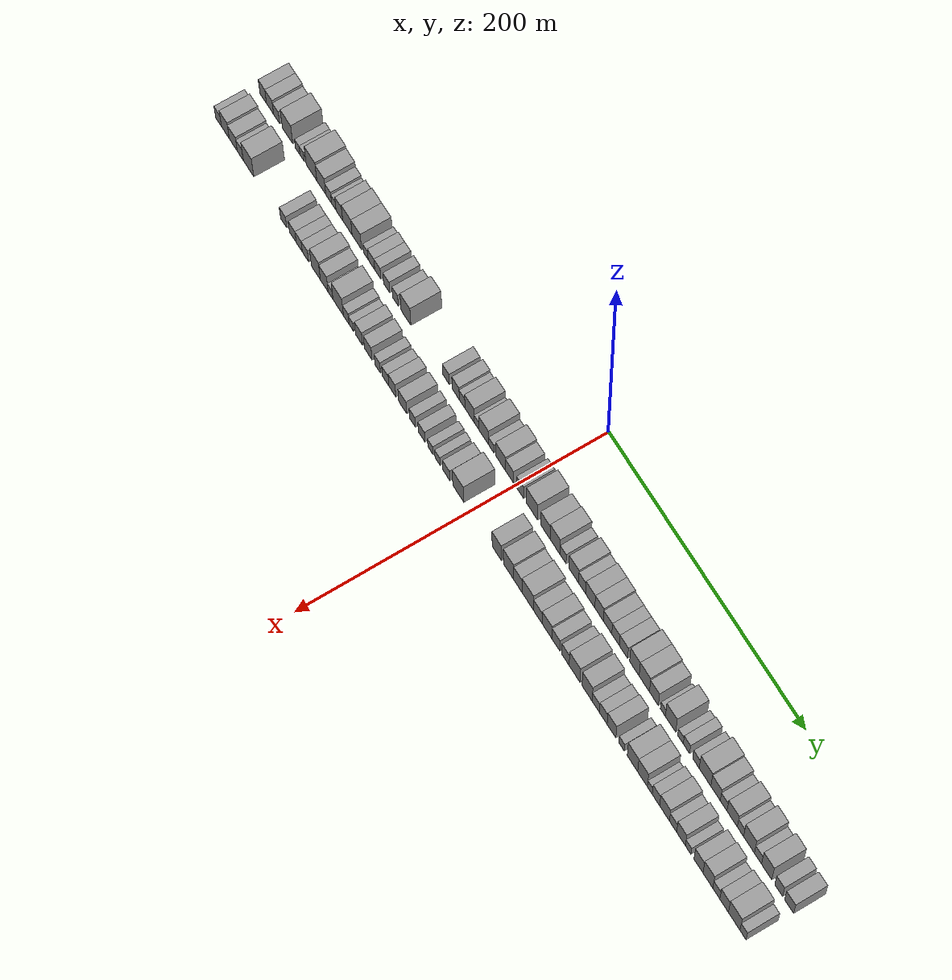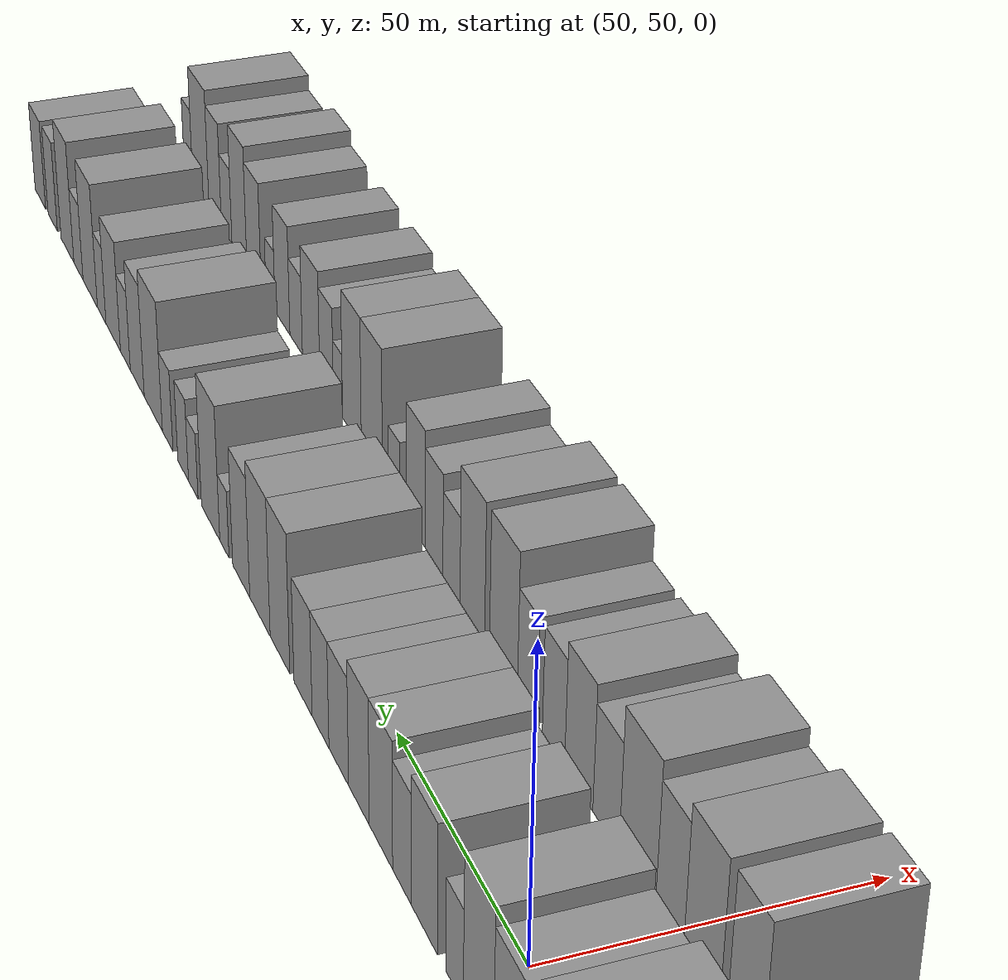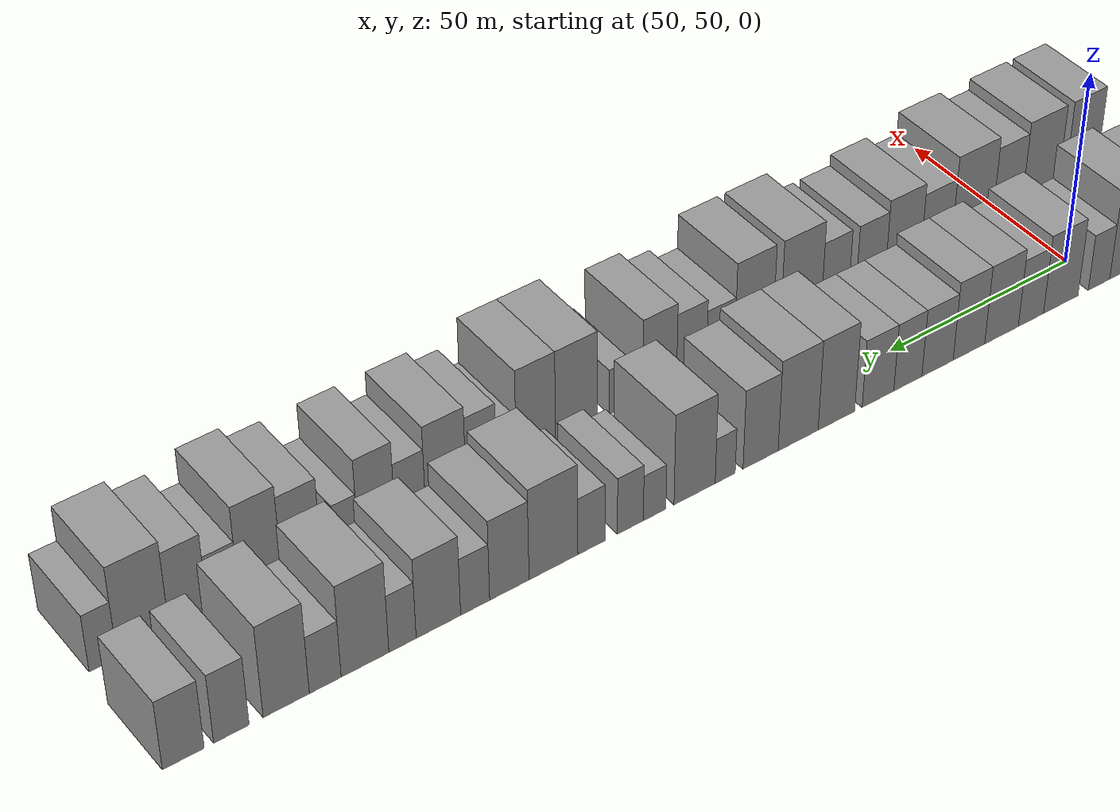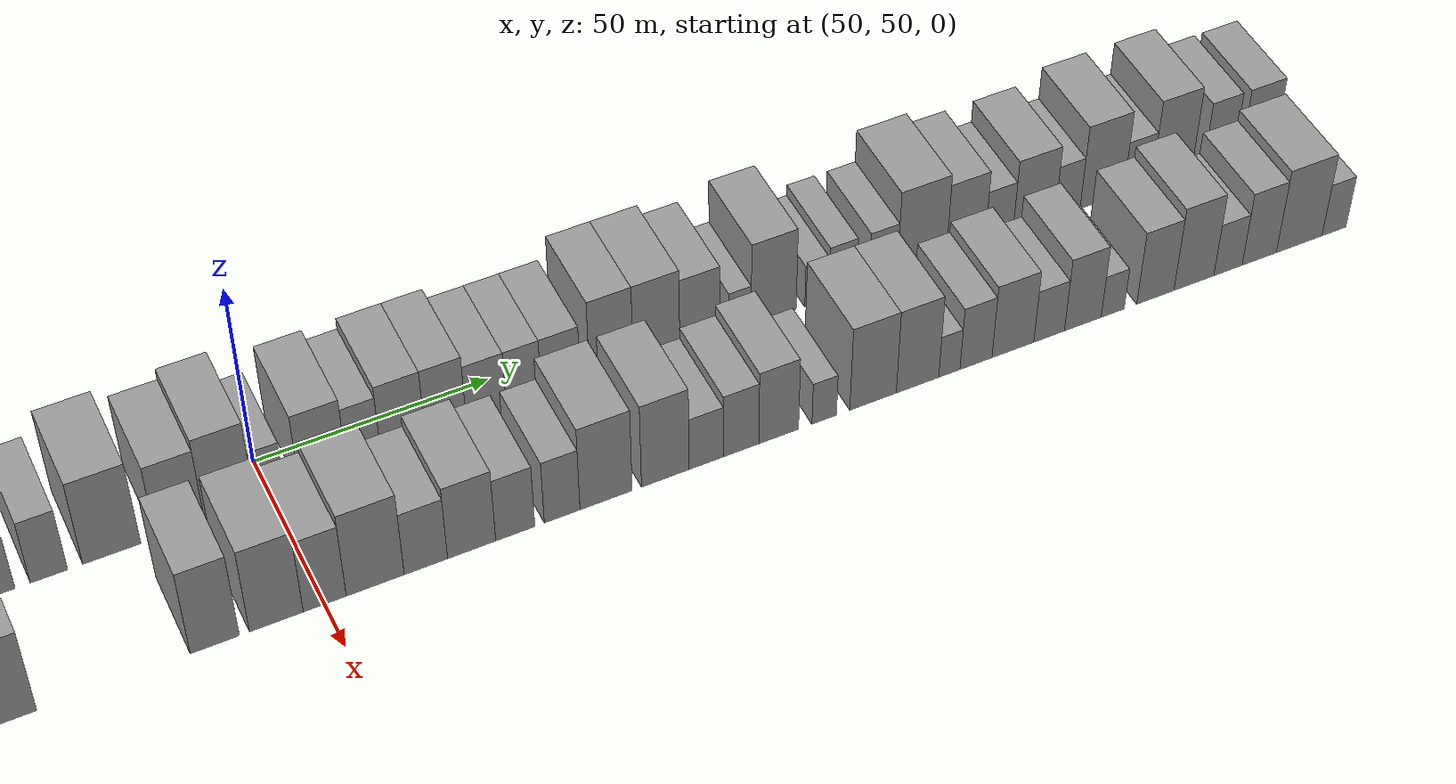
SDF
<sdf version="1.6">
 <world name="default">
  <scene>
   <sky><clouds><speed>12</speed></clouds></sky>
   <ambient>0.4 0.4 0.4 1</ambient>
   <background>0.7 0.7 0.7 1</background>
   <shadows>1</shadows>
  </scene>
  <gravity>0 0 -9.8066</gravity>
  <magnetic_field>6e-06 2.3e-05 -4.2e-05</magnetic_field>
  <physics default="0" name="default_physics" type="ode">
   <ode>
    <solver>
     <type>quick</type>
     <iters>10</iters>
     <sor>1.0</sor>
     <use_dynamic_moi_rescaling>0</use_dynamic_moi_rescaling>
    </solver>
    <constraints>
     <cfm>0</cfm>
     <erp>0.2</erp>
     <contact_max_correcting_vel>100</contact_max_correcting_vel>
     <contact_surface_layer>0.001</contact_surface_layer>
    </constraints>
   </ode>
   <max_step_size>0.004</max_step_size>
   <real_time_factor>1</real_time_factor>
   <real_time_update_rate>250</real_time_update_rate>
  </physics>
  <light name="sun" type="directional">
   <pose>0 0 10 0 0 0</pose>
   <diffuse>0.8 0.8 0.8 1</diffuse>
   <specular>0.2 0.2 0.2 1</specular>
   <attenuation>
    <range>1000</range>
    <constant>0.9</constant>
    <linear>0.01</linear>
    <quadratic>0.001</quadratic>
   </attenuation>
   <direction>-0.5 0.1 -0.9</direction>
  </light>
  <model name="building_1">
   <static>1</static>
   <pose>50.0000 -274.2942 0 0.000000 0.000000 0.000000</pose>
   <link name="link">
    <pose>0 0 9.00 0 0 0</pose>
    <collision name="collision"><geometry><box><size>20.0000 7.4115 18.0000</size></box></geometry></collision>
    <visual name="visual">
     <cast_shadows>0</cast_shadows>
     <geometry><box><size>20.0000 7.4115 18.0000</size></box></geometry>
     <material>
      <script>
       <uri>model://grey_wall/materials/scripts</uri>
       <uri>model://grey_wall/materials/textures</uri>
       <name>vrc/grey_wall</name>
      </script>
     </material>
    </visual>
   </link>
  </model>
  <model name="building_2">
   <static>1</static>
   <pose>50.0000 -266.5781 0 0.000000 0.000000 0.000000</pose>
   <link name="link">
    <pose>0 0 9.00 0 0 0</pose>
    <collision name="collision"><geometry><box><size>20.0000 8.0207 18.0000</size></box></geometry></collision>
    <visual name="visual">
     <cast_shadows>0</cast_shadows>
     <geometry><box><size>20.0000 8.0207 18.0000</size></box></geometry>
     <material>
      <script>
       <uri>model://grey_wall/materials/scripts</uri>
       <uri>model://grey_wall/materials/textures</uri>
       <name>vrc/grey_wall</name>
      </script>
     </material>
    </visual>
   </link>
  </model>
  <model name="building_3">
   <static>1</static>
   <pose>50.0000 -259.1972 0 0.000000 0.000000 0.000000</pose>
   <link name="link">
    <pose>0 0 7.50 0 0 0</pose>
    <collision name="collision"><geometry><box><size>20.0000 6.7413 15.0000</size></box></geometry></collision>
    <visual name="visual">
     <cast_shadows>0</cast_shadows>
     <geometry><box><size>20.0000 6.7413 15.0000</size></box></geometry>
     <material>
      <script>
       <uri>model://grey_wall/materials/scripts</uri>
       <uri>model://grey_wall/materials/textures</uri>
       <name>vrc/grey_wall</name>
      </script>
     </material>
    </visual>
   </link>
  </model>
  <model name="building_4">
   <static>1</static>
   <pose>50.0000 -246.9662 0 0.000000 0.000000 0.000000</pose>
   <link name="link">
    <pose>0 0 12.00 0 0 0</pose>
    <collision name="collision"><geometry><box><size>20.0000 11.7208 24.0000</size></box></geometry></collision>
    <visual name="visual">
     <cast_shadows>0</cast_shadows>
     <geometry><box><size>20.0000 11.7208 24.0000</size></box></geometry>
     <material>
      <script>
       <uri>model://grey_wall/materials/scripts</uri>
       <uri>model://grey_wall/materials/textures</uri>
       <name>vrc/grey_wall</name>
      </script>
     </material>
    </visual>
   </link>
  </model>
  <model name="building_5">
   <static>1</static>
   <pose>50.0000 -235.5989 0 0.000000 0.000000 0.000000</pose>
   <link name="link">
    <pose>0 0 6.00 0 0 0</pose>
    <collision name="collision"><geometry><box><size>20.0000 5.0137 12.0000</size></box></geometry></collision>
    <visual name="visual">
     <cast_shadows>0</cast_shadows>
     <geometry><box><size>20.0000 5.0137 12.0000</size></box></geometry>
     <material>
      <script>
       <uri>model://grey_wall/materials/scripts</uri>
       <uri>model://grey_wall/materials/textures</uri>
       <name>vrc/grey_wall</name>
      </script>
     </material>
    </visual>
   </link>
  </model>
  <model name="building_6">
   <static>1</static>
   <pose>50.0000 -230.6536 0 0.000000 0.000000 0.000000</pose>
   <link name="link">
    <pose>0 0 6.00 0 0 0</pose>
    <collision name="collision"><geometry><box><size>20.0000 4.8768 12.0000</size></box></geometry></collision>
    <visual name="visual">
     <cast_shadows>0</cast_shadows>
     <geometry><box><size>20.0000 4.8768 12.0000</size></box></geometry>
     <material>
      <script>
       <uri>model://grey_wall/materials/scripts</uri>
       <uri>model://grey_wall/materials/textures</uri>
       <name>vrc/grey_wall</name>
      </script>
     </material>
    </visual>
   </link>
  </model>
  <model name="building_7">
   <static>1</static>
   <pose>50.0000 -220.2989 0 0.000000 0.000000 0.000000</pose>
   <link name="link">
    <pose>0 0 12.00 0 0 0</pose>
    <collision name="collision"><geometry><box><size>20.0000 11.8327 24.0000</size></box></geometry></collision>
    <visual name="visual">
     <cast_shadows>0</cast_shadows>
     <geometry><box><size>20.0000 11.8327 24.0000</size></box></geometry>
     <material>
      <script>
       <uri>model://grey_wall/materials/scripts</uri>
       <uri>model://grey_wall/materials/textures</uri>
       <name>vrc/grey_wall</name>
      </script>
     </material>
    </visual>
   </link>
  </model>
  <model name="building_8">
   <static>1</static>
   <pose>50.0000 -209.4191 0 0.000000 0.000000 0.000000</pose>
   <link name="link">
    <pose>0 0 10.50 0 0 0</pose>
    <collision name="collision"><geometry><box><size>20.0000 9.9268 21.0000</size></box></geometry></collision>
    <visual name="visual">
     <cast_shadows>0</cast_shadows>
     <geometry><box><size>20.0000 9.9268 21.0000</size></box></geometry>
     <material>
      <script>
       <uri>model://grey_wall/materials/scripts</uri>
       <uri>model://grey_wall/materials/textures</uri>
       <name>vrc/grey_wall</name>
      </script>
     </material>
    </visual>
   </link>
  </model>
  <model name="building_9">
   <static>1</static>
   <pose>50.0000 -201.1970 0 0.000000 0.000000 0.000000</pose>
   <link name="link">
    <pose>0 0 7.50 0 0 0</pose>
    <collision name="collision"><geometry><box><size>20.0000 6.5175 15.0000</size></box></geometry></collision>
    <visual name="visual">
     <cast_shadows>0</cast_shadows>
     <geometry><box><size>20.0000 6.5175 15.0000</size></box></geometry>
     <material>
      <script>
       <uri>model://grey_wall/materials/scripts</uri>
       <uri>model://grey_wall/materials/textures</uri>
       <name>vrc/grey_wall</name>
      </script>
     </material>
    </visual>
   </link>
  </model>
  <model name="building_10">
   <static>1</static>
   <pose>50.0000 -195.5198 0 0.000000 0.000000 0.000000</pose>
   <link name="link">
    <pose>0 0 6.00 0 0 0</pose>
    <collision name="collision"><geometry><box><size>20.0000 4.8368 12.0000</size></box></geometry></collision>
    <visual name="visual">
     <cast_shadows>0</cast_shadows>
     <geometry><box><size>20.0000 4.8368 12.0000</size></box></geometry>
     <material>
      <script>
       <uri>model://grey_wall/materials/scripts</uri>
       <uri>model://grey_wall/materials/textures</uri>
       <name>vrc/grey_wall</name>
      </script>
     </material>
    </visual>
   </link>
  </model>
  <model name="building_11">
   <static>1</static>
   <pose>50.0000 -189.4424 0 0.000000 0.000000 0.000000</pose>
   <link name="link">
    <pose>0 0 9.00 0 0 0</pose>
    <collision name="collision"><geometry><box><size>20.0000 7.3181 18.0000</size></box></geometry></collision>
    <visual name="visual">
     <cast_shadows>0</cast_shadows>
     <geometry><box><size>20.0000 7.3181 18.0000</size></box></geometry>
     <material>
      <script>
       <uri>model://grey_wall/materials/scripts</uri>
       <uri>model://grey_wall/materials/textures</uri>
       <name>vrc/grey_wall</name>
      </script>
     </material>
    </visual>
   </link>
  </model>
  <model name="building_12">
   <static>1</static>
   <pose>50.0000 -180.5593 0 0.000000 0.000000 0.000000</pose>
   <link name="link">
    <pose>0 0 10.50 0 0 0</pose>
    <collision name="collision"><geometry><box><size>20.0000 10.4481 21.0000</size></box></geometry></collision>
    <visual name="visual">
     <cast_shadows>0</cast_shadows>
     <geometry><box><size>20.0000 10.4481 21.0000</size></box></geometry>
     <material>
      <script>
       <uri>model://grey_wall/materials/scripts</uri>
       <uri>model://grey_wall/materials/textures</uri>
       <name>vrc/grey_wall</name>
      </script>
     </material>
    </visual>
   </link>
  </model>
  <model name="building_13">
   <static>1</static>
   <pose>50.0000 -170.1561 0 0.000000 0.000000 0.000000</pose>
   <link name="link">
    <pose>0 0 10.50 0 0 0</pose>
    <collision name="collision"><geometry><box><size>20.0000 10.3582 21.0000</size></box></geometry></collision>
    <visual name="visual">
     <cast_shadows>0</cast_shadows>
     <geometry><box><size>20.0000 10.3582 21.0000</size></box></geometry>
     <material>
      <script>
       <uri>model://grey_wall/materials/scripts</uri>
       <uri>model://grey_wall/materials/textures</uri>
       <name>vrc/grey_wall</name>
      </script>
     </material>
    </visual>
   </link>
  </model>
  <model name="building_14">
   <static>1</static>
   <pose>50.0000 -160.3472 0 0.000000 0.000000 0.000000</pose>
   <link name="link">
    <pose>0 0 6.00 0 0 0</pose>
    <collision name="collision"><geometry><box><size>20.0000 5.2596 12.0000</size></box></geometry></collision>
    <visual name="visual">
     <cast_shadows>0</cast_shadows>
     <geometry><box><size>20.0000 5.2596 12.0000</size></box></geometry>
     <material>
      <script>
       <uri>model://grey_wall/materials/scripts</uri>
       <uri>model://grey_wall/materials/textures</uri>
       <name>vrc/grey_wall</name>
      </script>
     </material>
    </visual>
   </link>
  </model>
  <model name="building_15">
   <static>1</static>
   <pose>50.0000 -154.1600 0 0.000000 0.000000 0.000000</pose>
   <link name="link">
    <pose>0 0 7.50 0 0 0</pose>
    <collision name="collision"><geometry><box><size>20.0000 7.1147 15.0000</size></box></geometry></collision>
    <visual name="visual">
     <cast_shadows>0</cast_shadows>
     <geometry><box><size>20.0000 7.1147 15.0000</size></box></geometry>
     <material>
      <script>
       <uri>model://grey_wall/materials/scripts</uri>
       <uri>model://grey_wall/materials/textures</uri>
       <name>vrc/grey_wall</name>
      </script>
     </material>
    </visual>
   </link>
  </model>
  <model name="building_16">
   <static>1</static>
   <pose>50.0000 -147.2636 0 0.000000 0.000000 0.000000</pose>
   <link name="link">
    <pose>0 0 7.50 0 0 0</pose>
    <collision name="collision"><geometry><box><size>20.0000 6.6780 15.0000</size></box></geometry></collision>
    <visual name="visual">
     <cast_shadows>0</cast_shadows>
     <geometry><box><size>20.0000 6.6780 15.0000</size></box></geometry>
     <material>
      <script>
       <uri>model://grey_wall/materials/scripts</uri>
       <uri>model://grey_wall/materials/textures</uri>
       <name>vrc/grey_wall</name>
      </script>
     </material>
    </visual>
   </link>
  </model>
  <model name="building_17">
   <static>1</static>
   <pose>50.0000 -137.5323 0 0.000000 0.000000 0.000000</pose>
   <link name="link">
    <pose>0 0 7.50 0 0 0</pose>
    <collision name="collision"><geometry><box><size>20.0000 6.7847 15.0000</size></box></geometry></collision>
    <visual name="visual">
     <cast_shadows>0</cast_shadows>
     <geometry><box><size>20.0000 6.7847 15.0000</size></box></geometry>
     <material>
      <script>
       <uri>model://grey_wall/materials/scripts</uri>
       <uri>model://grey_wall/materials/textures</uri>
       <name>vrc/grey_wall</name>
      </script>
     </material>
    </visual>
   </link>
  </model>
  <model name="building_18">
   <static>1</static>
   <pose>50.0000 -128.0251 0 0.000000 0.000000 0.000000</pose>
   <link name="link">
    <pose>0 0 7.50 0 0 0</pose>
    <collision name="collision"><geometry><box><size>20.0000 6.2296 15.0000</size></box></geometry></collision>
    <visual name="visual">
     <cast_shadows>0</cast_shadows>
     <geometry><box><size>20.0000 6.2296 15.0000</size></box></geometry>
     <material>
      <script>
       <uri>model://grey_wall/materials/scripts</uri>
       <uri>model://grey_wall/materials/textures</uri>
       <name>vrc/grey_wall</name>
      </script>
     </material>
    </visual>
   </link>
  </model>
  <model name="building_19">
   <static>1</static>
   <pose>50.0000 -116.5922 0 0.000000 0.000000 0.000000</pose>
   <link name="link">
    <pose>0 0 12.00 0 0 0</pose>
    <collision name="collision"><geometry><box><size>20.0000 10.6363 24.0000</size></box></geometry></collision>
    <visual name="visual">
     <cast_shadows>0</cast_shadows>
     <geometry><box><size>20.0000 10.6363 24.0000</size></box></geometry>
     <material>
      <script>
       <uri>model://grey_wall/materials/scripts</uri>
       <uri>model://grey_wall/materials/textures</uri>
       <name>vrc/grey_wall</name>
      </script>
     </material>
    </visual>
   </link>
  </model>
  <model name="building_20">
   <static>1</static>
   <pose>50.0000 -73.4680 0 0.000000 0.000000 0.000000</pose>
   <link name="link">
    <pose>0 0 7.50 0 0 0</pose>
    <collision name="collision"><geometry><box><size>20.0000 7.2040 15.0000</size></box></geometry></collision>
    <visual name="visual">
     <cast_shadows>0</cast_shadows>
     <geometry><box><size>20.0000 7.2040 15.0000</size></box></geometry>
     <material>
      <script>
       <uri>model://grey_wall/materials/scripts</uri>
       <uri>model://grey_wall/materials/textures</uri>
       <name>vrc/grey_wall</name>
      </script>
     </material>
    </visual>
   </link>
  </model>
  <model name="building_21">
   <static>1</static>
   <pose>50.0000 -63.0588 0 0.000000 0.000000 0.000000</pose>
   <link name="link">
    <pose>0 0 9.00 0 0 0</pose>
    <collision name="collision"><geometry><box><size>20.0000 7.6144 18.0000</size></box></geometry></collision>
    <visual name="visual">
     <cast_shadows>0</cast_shadows>
     <geometry><box><size>20.0000 7.6144 18.0000</size></box></geometry>
     <material>
      <script>
       <uri>model://grey_wall/materials/scripts</uri>
       <uri>model://grey_wall/materials/textures</uri>
       <name>vrc/grey_wall</name>
      </script>
     </material>
    </visual>
   </link>
  </model>
  <model name="building_22">
   <static>1</static>
   <pose>50.0000 -56.2513 0 0.000000 0.000000 0.000000</pose>
   <link name="link">
    <pose>0 0 7.50 0 0 0</pose>
    <collision name="collision"><geometry><box><size>20.0000 6.0006 15.0000</size></box></geometry></collision>
    <visual name="visual">
     <cast_shadows>0</cast_shadows>
     <geometry><box><size>20.0000 6.0006 15.0000</size></box></geometry>
     <material>
      <script>
       <uri>model://grey_wall/materials/scripts</uri>
       <uri>model://grey_wall/materials/textures</uri>
       <name>vrc/grey_wall</name>
      </script>
     </material>
    </visual>
   </link>
  </model>
  <model name="building_23">
   <static>1</static>
   <pose>50.0000 -48.2686 0 0.000000 0.000000 0.000000</pose>
   <link name="link">
    <pose>0 0 10.50 0 0 0</pose>
    <collision name="collision"><geometry><box><size>20.0000 9.9647 21.0000</size></box></geometry></collision>
    <visual name="visual">
     <cast_shadows>0</cast_shadows>
     <geometry><box><size>20.0000 9.9647 21.0000</size></box></geometry>
     <material>
      <script>
       <uri>model://grey_wall/materials/scripts</uri>
       <uri>model://grey_wall/materials/textures</uri>
       <name>vrc/grey_wall</name>
      </script>
     </material>
    </visual>
   </link>
  </model>
  <model name="building_24">
   <static>1</static>
   <pose>50.0000 -40.8244 0 0.000000 0.000000 0.000000</pose>
   <link name="link">
    <pose>0 0 6.00 0 0 0</pose>
    <collision name="collision"><geometry><box><size>20.0000 4.9237 12.0000</size></box></geometry></collision>
    <visual name="visual">
     <cast_shadows>0</cast_shadows>
     <geometry><box><size>20.0000 4.9237 12.0000</size></box></geometry>
     <material>
      <script>
       <uri>model://grey_wall/materials/scripts</uri>
       <uri>model://grey_wall/materials/textures</uri>
       <name>vrc/grey_wall</name>
      </script>
     </material>
    </visual>
   </link>
  </model>
  <model name="building_25">
   <static>1</static>
   <pose>50.0000 -33.2198 0 0.000000 0.000000 0.000000</pose>
   <link name="link">
    <pose>0 0 10.50 0 0 0</pose>
    <collision name="collision"><geometry><box><size>20.0000 10.2856 21.0000</size></box></geometry></collision>
    <visual name="visual">
     <cast_shadows>0</cast_shadows>
     <geometry><box><size>20.0000 10.2856 21.0000</size></box></geometry>
     <material>
      <script>
       <uri>model://grey_wall/materials/scripts</uri>
       <uri>model://grey_wall/materials/textures</uri>
       <name>vrc/grey_wall</name>
      </script>
     </material>
    </visual>
   </link>
  </model>
  <model name="building_26">
   <static>1</static>
   <pose>50.0000 -25.3277 0 0.000000 0.000000 0.000000</pose>
   <link name="link">
    <pose>0 0 6.00 0 0 0</pose>
    <collision name="collision"><geometry><box><size>20.0000 5.4986 12.0000</size></box></geometry></collision>
    <visual name="visual">
     <cast_shadows>0</cast_shadows>
     <geometry><box><size>20.0000 5.4986 12.0000</size></box></geometry>
     <material>
      <script>
       <uri>model://grey_wall/materials/scripts</uri>
       <uri>model://grey_wall/materials/textures</uri>
       <name>vrc/grey_wall</name>
      </script>
     </material>
    </visual>
   </link>
  </model>
  <model name="building_27">
   <static>1</static>
   <pose>50.0000 -15.3713 0 0.000000 0.000000 0.000000</pose>
   <link name="link">
    <pose>0 0 10.50 0 0 0</pose>
    <collision name="collision"><geometry><box><size>20.0000 10.4143 21.0000</size></box></geometry></collision>
    <visual name="visual">
     <cast_shadows>0</cast_shadows>
     <geometry><box><size>20.0000 10.4143 21.0000</size></box></geometry>
     <material>
      <script>
       <uri>model://grey_wall/materials/scripts</uri>
       <uri>model://grey_wall/materials/textures</uri>
       <name>vrc/grey_wall</name>
      </script>
     </material>
    </visual>
   </link>
  </model>
  <model name="building_28">
   <static>1</static>
   <pose>50.0000 -5.9716 0 0.000000 0.000000 0.000000</pose>
   <link name="link">
    <pose>0 0 9.00 0 0 0</pose>
    <collision name="collision"><geometry><box><size>20.0000 8.3850 18.0000</size></box></geometry></collision>
    <visual name="visual">
     <cast_shadows>0</cast_shadows>
     <geometry><box><size>20.0000 8.3850 18.0000</size></box></geometry>
     <material>
      <script>
       <uri>model://grey_wall/materials/scripts</uri>
       <uri>model://grey_wall/materials/textures</uri>
       <name>vrc/grey_wall</name>
      </script>
     </material>
    </visual>
   </link>
  </model>
  <model name="building_29">
   <static>1</static>
   <pose>50.0000 4.9267 0 0.000000 0.000000 0.000000</pose>
   <link name="link">
    <pose>0 0 9.00 0 0 0</pose>
    <collision name="collision"><geometry><box><size>20.0000 7.4116 18.0000</size></box></geometry></collision>
    <visual name="visual">
     <cast_shadows>0</cast_shadows>
     <geometry><box><size>20.0000 7.4116 18.0000</size></box></geometry>
     <material>
      <script>
       <uri>model://grey_wall/materials/scripts</uri>
       <uri>model://grey_wall/materials/textures</uri>
       <name>vrc/grey_wall</name>
      </script>
     </material>
    </visual>
   </link>
  </model>
  <model name="building_30">
   <static>1</static>
   <pose>50.0000 17.4689 0 0.000000 0.000000 0.000000</pose>
   <link name="link">
    <pose>0 0 12.00 0 0 0</pose>
    <collision name="collision"><geometry><box><size>20.0000 11.6728 24.0000</size></box></geometry></collision>
    <visual name="visual">
     <cast_shadows>0</cast_shadows>
     <geometry><box><size>20.0000 11.6728 24.0000</size></box></geometry>
     <material>
      <script>
       <uri>model://grey_wall/materials/scripts</uri>
       <uri>model://grey_wall/materials/textures</uri>
       <name>vrc/grey_wall</name>
      </script>
     </material>
    </visual>
   </link>
  </model>
  <model name="building_31">
   <static>1</static>
   <pose>50.0000 31.2855 0 0.000000 0.000000 0.000000</pose>
   <link name="link">
    <pose>0 0 10.50 0 0 0</pose>
    <collision name="collision"><geometry><box><size>20.0000 9.9604 21.0000</size></box></geometry></collision>
    <visual name="visual">
     <cast_shadows>0</cast_shadows>
     <geometry><box><size>20.0000 9.9604 21.0000</size></box></geometry>
     <material>
      <script>
       <uri>model://grey_wall/materials/scripts</uri>
       <uri>model://grey_wall/materials/textures</uri>
       <name>vrc/grey_wall</name>
      </script>
     </material>
    </visual>
   </link>
  </model>
  <model name="building_32">
   <static>1</static>
   <pose>50.0000 41.4286 0 0.000000 0.000000 0.000000</pose>
   <link name="link">
    <pose>0 0 12.00 0 0 0</pose>
    <collision name="collision"><geometry><box><size>20.0000 10.3258 24.0000</size></box></geometry></collision>
    <visual name="visual">
     <cast_shadows>0</cast_shadows>
     <geometry><box><size>20.0000 10.3258 24.0000</size></box></geometry>
     <material>
      <script>
       <uri>model://grey_wall/materials/scripts</uri>
       <uri>model://grey_wall/materials/textures</uri>
       <name>vrc/grey_wall</name>
      </script>
     </material>
    </visual>
   </link>
  </model>
  <model name="building_33">
   <static>1</static>
   <pose>50.0000 49.7186 0 0.000000 0.000000 0.000000</pose>
   <link name="link">
    <pose>0 0 7.50 0 0 0</pose>
    <collision name="collision"><geometry><box><size>20.0000 6.2543 15.0000</size></box></geometry></collision>
    <visual name="visual">
     <cast_shadows>0</cast_shadows>
     <geometry><box><size>20.0000 6.2543 15.0000</size></box></geometry>
     <material>
      <script>
       <uri>model://grey_wall/materials/scripts</uri>
       <uri>model://grey_wall/materials/textures</uri>
       <name>vrc/grey_wall</name>
      </script>
     </material>
    </visual>
   </link>
  </model>
  <model name="building_34">
   <static>1</static>
   <pose>50.0000 60.8240 0 0.000000 0.000000 0.000000</pose>
   <link name="link">
    <pose>0 0 10.50 0 0 0</pose>
    <collision name="collision"><geometry><box><size>20.0000 9.9564 21.0000</size></box></geometry></collision>
    <visual name="visual">
     <cast_shadows>0</cast_shadows>
     <geometry><box><size>20.0000 9.9564 21.0000</size></box></geometry>
     <material>
      <script>
       <uri>model://grey_wall/materials/scripts</uri>
       <uri>model://grey_wall/materials/textures</uri>
       <name>vrc/grey_wall</name>
      </script>
     </material>
    </visual>
   </link>
  </model>
  <model name="building_35">
   <static>1</static>
   <pose>50.0000 69.4040 0 0.000000 0.000000 0.000000</pose>
   <link name="link">
    <pose>0 0 9.00 0 0 0</pose>
    <collision name="collision"><geometry><box><size>20.0000 7.2037 18.0000</size></box></geometry></collision>
    <visual name="visual">
     <cast_shadows>0</cast_shadows>
     <geometry><box><size>20.0000 7.2037 18.0000</size></box></geometry>
     <material>
      <script>
       <uri>model://grey_wall/materials/scripts</uri>
       <uri>model://grey_wall/materials/textures</uri>
       <name>vrc/grey_wall</name>
      </script>
     </material>
    </visual>
   </link>
  </model>
  <model name="building_36">
   <static>1</static>
   <pose>50.0000 77.7374 0 0.000000 0.000000 0.000000</pose>
   <link name="link">
    <pose>0 0 10.50 0 0 0</pose>
    <collision name="collision"><geometry><box><size>20.0000 9.4630 21.0000</size></box></geometry></collision>
    <visual name="visual">
     <cast_shadows>0</cast_shadows>
     <geometry><box><size>20.0000 9.4630 21.0000</size></box></geometry>
     <material>
      <script>
       <uri>model://grey_wall/materials/scripts</uri>
       <uri>model://grey_wall/materials/textures</uri>
       <name>vrc/grey_wall</name>
      </script>
     </material>
    </visual>
   </link>
  </model>
  <model name="building_37">
   <static>1</static>
   <pose>50.0000 86.8551 0 0.000000 0.000000 0.000000</pose>
   <link name="link">
    <pose>0 0 10.50 0 0 0</pose>
    <collision name="collision"><geometry><box><size>20.0000 8.7724 21.0000</size></box></geometry></collision>
    <visual name="visual">
     <cast_shadows>0</cast_shadows>
     <geometry><box><size>20.0000 8.7724 21.0000</size></box></geometry>
     <material>
      <script>
       <uri>model://grey_wall/materials/scripts</uri>
       <uri>model://grey_wall/materials/textures</uri>
       <name>vrc/grey_wall</name>
      </script>
     </material>
    </visual>
   </link>
  </model>
  <model name="building_38">
   <static>1</static>
   <pose>50.0000 95.5552 0 0.000000 0.000000 0.000000</pose>
   <link name="link">
    <pose>0 0 9.00 0 0 0</pose>
    <collision name="collision"><geometry><box><size>20.0000 8.6279 18.0000</size></box></geometry></collision>
    <visual name="visual">
     <cast_shadows>0</cast_shadows>
     <geometry><box><size>20.0000 8.6279 18.0000</size></box></geometry>
     <material>
      <script>
       <uri>model://grey_wall/materials/scripts</uri>
       <uri>model://grey_wall/materials/textures</uri>
       <name>vrc/grey_wall</name>
      </script>
     </material>
    </visual>
   </link>
  </model>
  <model name="building_39">
   <static>1</static>
   <pose>50.0000 103.6890 0 0.000000 0.000000 0.000000</pose>
   <link name="link">
    <pose>0 0 9.00 0 0 0</pose>
    <collision name="collision"><geometry><box><size>20.0000 7.6397 18.0000</size></box></geometry></collision>
    <visual name="visual">
     <cast_shadows>0</cast_shadows>
     <geometry><box><size>20.0000 7.6397 18.0000</size></box></geometry>
     <material>
      <script>
       <uri>model://grey_wall/materials/scripts</uri>
       <uri>model://grey_wall/materials/textures</uri>
       <name>vrc/grey_wall</name>
      </script>
     </material>
    </visual>
   </link>
  </model>
  <model name="building_40">
   <static>1</static>
   <pose>50.0000 111.7709 0 0.000000 0.000000 0.000000</pose>
   <link name="link">
    <pose>0 0 9.00 0 0 0</pose>
    <collision name="collision"><geometry><box><size>20.0000 8.5241 18.0000</size></box></geometry></collision>
    <visual name="visual">
     <cast_shadows>0</cast_shadows>
     <geometry><box><size>20.0000 8.5241 18.0000</size></box></geometry>
     <material>
      <script>
       <uri>model://grey_wall/materials/scripts</uri>
       <uri>model://grey_wall/materials/textures</uri>
       <name>vrc/grey_wall</name>
      </script>
     </material>
    </visual>
   </link>
  </model>
  <model name="building_41">
   <static>1</static>
   <pose>50.0000 122.8686 0 0.000000 0.000000 0.000000</pose>
   <link name="link">
    <pose>0 0 12.00 0 0 0</pose>
    <collision name="collision"><geometry><box><size>20.0000 9.6714 24.0000</size></box></geometry></collision>
    <visual name="visual">
     <cast_shadows>0</cast_shadows>
     <geometry><box><size>20.0000 9.6714 24.0000</size></box></geometry>
     <material>
      <script>
       <uri>model://grey_wall/materials/scripts</uri>
       <uri>model://grey_wall/materials/textures</uri>
       <name>vrc/grey_wall</name>
      </script>
     </material>
    </visual>
   </link>
  </model>
  <model name="building_42">
   <static>1</static>
   <pose>50.0000 132.9142 0 0.000000 0.000000 0.000000</pose>
   <link name="link">
    <pose>0 0 12.00 0 0 0</pose>
    <collision name="collision"><geometry><box><size>20.0000 10.4198 24.0000</size></box></geometry></collision>
    <visual name="visual">
     <cast_shadows>0</cast_shadows>
     <geometry><box><size>20.0000 10.4198 24.0000</size></box></geometry>
     <material>
      <script>
       <uri>model://grey_wall/materials/scripts</uri>
       <uri>model://grey_wall/materials/textures</uri>
       <name>vrc/grey_wall</name>
      </script>
     </material>
    </visual>
   </link>
  </model>
  <model name="building_43">
   <static>1</static>
   <pose>50.0000 142.6442 0 0.000000 0.000000 0.000000</pose>
   <link name="link">
    <pose>0 0 10.50 0 0 0</pose>
    <collision name="collision"><geometry><box><size>20.0000 9.0402 21.0000</size></box></geometry></collision>
    <visual name="visual">
     <cast_shadows>0</cast_shadows>
     <geometry><box><size>20.0000 9.0402 21.0000</size></box></geometry>
     <material>
      <script>
       <uri>model://grey_wall/materials/scripts</uri>
       <uri>model://grey_wall/materials/textures</uri>
       <name>vrc/grey_wall</name>
      </script>
     </material>
    </visual>
   </link>
  </model>
  <model name="building_44">
   <static>1</static>
   <pose>50.0000 151.7030 0 0.000000 0.000000 0.000000</pose>
   <link name="link">
    <pose>0 0 6.00 0 0 0</pose>
    <collision name="collision"><geometry><box><size>20.0000 5.0773 12.0000</size></box></geometry></collision>
    <visual name="visual">
     <cast_shadows>0</cast_shadows>
     <geometry><box><size>20.0000 5.0773 12.0000</size></box></geometry>
     <material>
      <script>
       <uri>model://grey_wall/materials/scripts</uri>
       <uri>model://grey_wall/materials/textures</uri>
       <name>vrc/grey_wall</name>
      </script>
     </material>
    </visual>
   </link>
  </model>
  <model name="building_45">
   <static>1</static>
   <pose>50.0000 159.4163 0 0.000000 0.000000 0.000000</pose>
   <link name="link">
    <pose>0 0 12.00 0 0 0</pose>
    <collision name="collision"><geometry><box><size>20.0000 10.3494 24.0000</size></box></geometry></collision>
    <visual name="visual">
     <cast_shadows>0</cast_shadows>
     <geometry><box><size>20.0000 10.3494 24.0000</size></box></geometry>
     <material>
      <script>
       <uri>model://grey_wall/materials/scripts</uri>
       <uri>model://grey_wall/materials/textures</uri>
       <name>vrc/grey_wall</name>
      </script>
     </material>
    </visual>
   </link>
  </model>
  <model name="building_46">
   <static>1</static>
   <pose>50.0000 169.3795 0 0.000000 0.000000 0.000000</pose>
   <link name="link">
    <pose>0 0 6.00 0 0 0</pose>
    <collision name="collision"><geometry><box><size>20.0000 5.5770 12.0000</size></box></geometry></collision>
    <visual name="visual">
     <cast_shadows>0</cast_shadows>
     <geometry><box><size>20.0000 5.5770 12.0000</size></box></geometry>
     <material>
      <script>
       <uri>model://grey_wall/materials/scripts</uri>
       <uri>model://grey_wall/materials/textures</uri>
       <name>vrc/grey_wall</name>
      </script>
     </material>
    </visual>
   </link>
  </model>
  <model name="building_47">
   <static>1</static>
   <pose>50.0000 175.3558 0 0.000000 0.000000 0.000000</pose>
   <link name="link">
    <pose>0 0 7.50 0 0 0</pose>
    <collision name="collision"><geometry><box><size>20.0000 6.3758 15.0000</size></box></geometry></collision>
    <visual name="visual">
     <cast_shadows>0</cast_shadows>
     <geometry><box><size>20.0000 6.3758 15.0000</size></box></geometry>
     <material>
      <script>
       <uri>model://grey_wall/materials/scripts</uri>
       <uri>model://grey_wall/materials/textures</uri>
       <name>vrc/grey_wall</name>
      </script>
     </material>
    </visual>
   </link>
  </model>
  <model name="building_48">
   <static>1</static>
   <pose>50.0000 184.8294 0 0.000000 0.000000 0.000000</pose>
   <link name="link">
    <pose>0 0 7.50 0 0 0</pose>
    <collision name="collision"><geometry><box><size>20.0000 6.5715 15.0000</size></box></geometry></collision>
    <visual name="visual">
     <cast_shadows>0</cast_shadows>
     <geometry><box><size>20.0000 6.5715 15.0000</size></box></geometry>
     <material>
      <script>
       <uri>model://grey_wall/materials/scripts</uri>
       <uri>model://grey_wall/materials/textures</uri>
       <name>vrc/grey_wall</name>
      </script>
     </material>
    </visual>
   </link>
  </model>
  <model name="building_49">
   <static>1</static>
   <pose>50.0000 193.9374 0 0.000000 0.000000 0.000000</pose>
   <link name="link">
    <pose>0 0 12.00 0 0 0</pose>
    <collision name="collision"><geometry><box><size>20.0000 11.6444 24.0000</size></box></geometry></collision>
    <visual name="visual">
     <cast_shadows>0</cast_shadows>
     <geometry><box><size>20.0000 11.6444 24.0000</size></box></geometry>
     <material>
      <script>
       <uri>model://grey_wall/materials/scripts</uri>
       <uri>model://grey_wall/materials/textures</uri>
       <name>vrc/grey_wall</name>
      </script>
     </material>
    </visual>
   </link>
  </model>
  <model name="building_50">
   <static>1</static>
   <pose>50.0000 204.3791 0 0.000000 0.000000 0.000000</pose>
   <link name="link">
    <pose>0 0 10.50 0 0 0</pose>
    <collision name="collision"><geometry><box><size>20.0000 9.2392 21.0000</size></box></geometry></collision>
    <visual name="visual">
     <cast_shadows>0</cast_shadows>
     <geometry><box><size>20.0000 9.2392 21.0000</size></box></geometry>
     <material>
      <script>
       <uri>model://grey_wall/materials/scripts</uri>
       <uri>model://grey_wall/materials/textures</uri>
       <name>vrc/grey_wall</name>
      </script>
     </material>
    </visual>
   </link>
  </model>
  <model name="building_51">
   <static>1</static>
   <pose>50.0000 212.3680 0 0.000000 0.000000 0.000000</pose>
   <link name="link">
    <pose>0 0 7.50 0 0 0</pose>
    <collision name="collision"><geometry><box><size>20.0000 6.7385 15.0000</size></box></geometry></collision>
    <visual name="visual">
     <cast_shadows>0</cast_shadows>
     <geometry><box><size>20.0000 6.7385 15.0000</size></box></geometry>
     <material>
      <script>
       <uri>model://grey_wall/materials/scripts</uri>
       <uri>model://grey_wall/materials/textures</uri>
       <name>vrc/grey_wall</name>
      </script>
     </material>
    </visual>
   </link>
  </model>
  <model name="building_52">
   <static>1</static>
   <pose>50.0000 220.8307 0 0.000000 0.000000 0.000000</pose>
   <link name="link">
    <pose>0 0 10.50 0 0 0</pose>
    <collision name="collision"><geometry><box><size>20.0000 10.1869 21.0000</size></box></geometry></collision>
    <visual name="visual">
     <cast_shadows>0</cast_shadows>
     <geometry><box><size>20.0000 10.1869 21.0000</size></box></geometry>
     <material>
      <script>
       <uri>model://grey_wall/materials/scripts</uri>
       <uri>model://grey_wall/materials/textures</uri>
       <name>vrc/grey_wall</name>
      </script>
     </material>
    </visual>
   </link>
  </model>
  <model name="building_53">
   <static>1</static>
   <pose>50.0000 229.0091 0 0.000000 0.000000 0.000000</pose>
   <link name="link">
    <pose>0 0 7.50 0 0 0</pose>
    <collision name="collision"><geometry><box><size>20.0000 6.1700 15.0000</size></box></geometry></collision>
    <visual name="visual">
     <cast_shadows>0</cast_shadows>
     <geometry><box><size>20.0000 6.1700 15.0000</size></box></geometry>
     <material>
      <script>
       <uri>model://grey_wall/materials/scripts</uri>
       <uri>model://grey_wall/materials/textures</uri>
       <name>vrc/grey_wall</name>
      </script>
     </material>
    </visual>
   </link>
  </model>
  <model name="building_54">
   <static>1</static>
   <pose>50.0000 237.4223 0 0.000000 0.000000 0.000000</pose>
   <link name="link">
    <pose>0 0 12.00 0 0 0</pose>
    <collision name="collision"><geometry><box><size>20.0000 10.6562 24.0000</size></box></geometry></collision>
    <visual name="visual">
     <cast_shadows>0</cast_shadows>
     <geometry><box><size>20.0000 10.6562 24.0000</size></box></geometry>
     <material>
      <script>
       <uri>model://grey_wall/materials/scripts</uri>
       <uri>model://grey_wall/materials/textures</uri>
       <name>vrc/grey_wall</name>
      </script>
     </material>
    </visual>
   </link>
  </model>
  <model name="building_55">
   <static>1</static>
   <pose>50.0000 246.2579 0 0.000000 0.000000 0.000000</pose>
   <link name="link">
    <pose>0 0 7.50 0 0 0</pose>
    <collision name="collision"><geometry><box><size>20.0000 7.0150 15.0000</size></box></geometry></collision>
    <visual name="visual">
     <cast_shadows>0</cast_shadows>
     <geometry><box><size>20.0000 7.0150 15.0000</size></box></geometry>
     <material>
      <script>
       <uri>model://grey_wall/materials/scripts</uri>
       <uri>model://grey_wall/materials/textures</uri>
       <name>vrc/grey_wall</name>
      </script>
     </material>
    </visual>
   </link>
  </model>
  <model name="building_56">
   <static>1</static>
   <pose>50.0000 254.7818 0 0.000000 0.000000 0.000000</pose>
   <link name="link">
    <pose>0 0 12.00 0 0 0</pose>
    <collision name="collision"><geometry><box><size>20.0000 10.0329 24.0000</size></box></geometry></collision>
    <visual name="visual">
     <cast_shadows>0</cast_shadows>
     <geometry><box><size>20.0000 10.0329 24.0000</size></box></geometry>
     <material>
      <script>
       <uri>model://grey_wall/materials/scripts</uri>
       <uri>model://grey_wall/materials/textures</uri>
       <name>vrc/grey_wall</name>
      </script>
     </material>
    </visual>
   </link>
  </model>
  <model name="building_57">
   <static>1</static>
   <pose>50.0000 266.5847 0 0.000000 0.000000 0.000000</pose>
   <link name="link">
    <pose>0 0 9.00 0 0 0</pose>
    <collision name="collision"><geometry><box><size>20.0000 7.5729 18.0000</size></box></geometry></collision>
    <visual name="visual">
     <cast_shadows>0</cast_shadows>
     <geometry><box><size>20.0000 7.5729 18.0000</size></box></geometry>
     <material>
      <script>
       <uri>model://grey_wall/materials/scripts</uri>
       <uri>model://grey_wall/materials/textures</uri>
       <name>vrc/grey_wall</name>
      </script>
     </material>
    </visual>
   </link>
  </model>
  <model name="building_58">
   <static>1</static>
   <pose>50.0000 276.7673 0 0.000000 0.000000 0.000000</pose>
   <link name="link">
    <pose>0 0 9.00 0 0 0</pose>
    <collision name="collision"><geometry><box><size>20.0000 8.7923 18.0000</size></box></geometry></collision>
    <visual name="visual">
     <cast_shadows>0</cast_shadows>
     <geometry><box><size>20.0000 8.7923 18.0000</size></box></geometry>
     <material>
      <script>
       <uri>model://grey_wall/materials/scripts</uri>
       <uri>model://grey_wall/materials/textures</uri>
       <name>vrc/grey_wall</name>
      </script>
     </material>
    </visual>
   </link>
  </model>
  <model name="building_59">
   <static>1</static>
   <pose>79.0000 -274.7064 0 0.000000 0.000000 0.000000</pose>
   <link name="link">
    <pose>0 0 7.50 0 0 0</pose>
    <collision name="collision"><geometry><box><size>20.0000 6.5872 15.0000</size></box></geometry></collision>
    <visual name="visual">
     <cast_shadows>0</cast_shadows>
     <geometry><box><size>20.0000 6.5872 15.0000</size></box></geometry>
     <material>
      <script>
       <uri>model://grey_wall/materials/scripts</uri>
       <uri>model://grey_wall/materials/textures</uri>
       <name>vrc/grey_wall</name>
      </script>
     </material>
    </visual>
   </link>
  </model>
  <model name="building_60">
   <static>1</static>
   <pose>79.0000 -266.9668 0 0.000000 0.000000 0.000000</pose>
   <link name="link">
    <pose>0 0 10.50 0 0 0</pose>
    <collision name="collision"><geometry><box><size>20.0000 8.8920 21.0000</size></box></geometry></collision>
    <visual name="visual">
     <cast_shadows>0</cast_shadows>
     <geometry><box><size>20.0000 8.8920 21.0000</size></box></geometry>
     <material>
      <script>
       <uri>model://grey_wall/materials/scripts</uri>
       <uri>model://grey_wall/materials/textures</uri>
       <name>vrc/grey_wall</name>
      </script>
     </material>
    </visual>
   </link>
  </model>
  <model name="building_61">
   <static>1</static>
   <pose>79.0000 -258.0597 0 0.000000 0.000000 0.000000</pose>
   <link name="link">
    <pose>0 0 9.00 0 0 0</pose>
    <collision name="collision"><geometry><box><size>20.0000 8.9222 18.0000</size></box></geometry></collision>
    <visual name="visual">
     <cast_shadows>0</cast_shadows>
     <geometry><box><size>20.0000 8.9222 18.0000</size></box></geometry>
     <material>
      <script>
       <uri>model://grey_wall/materials/scripts</uri>
       <uri>model://grey_wall/materials/textures</uri>
       <name>vrc/grey_wall</name>
      </script>
     </material>
    </visual>
   </link>
  </model>
  <model name="building_62">
   <static>1</static>
   <pose>79.0000 -250.1834 0 0.000000 0.000000 0.000000</pose>
   <link name="link">
    <pose>0 0 7.50 0 0 0</pose>
    <collision name="collision"><geometry><box><size>20.0000 6.8305 15.0000</size></box></geometry></collision>
    <visual name="visual">
     <cast_shadows>0</cast_shadows>
     <geometry><box><size>20.0000 6.8305 15.0000</size></box></geometry>
     <material>
      <script>
       <uri>model://grey_wall/materials/scripts</uri>
       <uri>model://grey_wall/materials/textures</uri>
       <name>vrc/grey_wall</name>
      </script>
     </material>
    </visual>
   </link>
  </model>
  <model name="building_63">
   <static>1</static>
   <pose>79.0000 -240.8535 0 0.000000 0.000000 0.000000</pose>
   <link name="link">
    <pose>0 0 12.00 0 0 0</pose>
    <collision name="collision"><geometry><box><size>20.0000 11.8293 24.0000</size></box></geometry></collision>
    <visual name="visual">
     <cast_shadows>0</cast_shadows>
     <geometry><box><size>20.0000 11.8293 24.0000</size></box></geometry>
     <material>
      <script>
       <uri>model://grey_wall/materials/scripts</uri>
       <uri>model://grey_wall/materials/textures</uri>
       <name>vrc/grey_wall</name>
      </script>
     </material>
    </visual>
   </link>
  </model>
  <model name="building_64">
   <static>1</static>
   <pose>79.0000 -201.6600 0 0.000000 0.000000 0.000000</pose>
   <link name="link">
    <pose>0 0 7.50 0 0 0</pose>
    <collision name="collision"><geometry><box><size>20.0000 6.8525 15.0000</size></box></geometry></collision>
    <visual name="visual">
     <cast_shadows>0</cast_shadows>
     <geometry><box><size>20.0000 6.8525 15.0000</size></box></geometry>
     <material>
      <script>
       <uri>model://grey_wall/materials/scripts</uri>
       <uri>model://grey_wall/materials/textures</uri>
       <name>vrc/grey_wall</name>
      </script>
     </material>
    </visual>
   </link>
  </model>
  <model name="building_65">
   <static>1</static>
   <pose>79.0000 -191.5080 0 0.000000 0.000000 0.000000</pose>
   <link name="link">
    <pose>0 0 7.50 0 0 0</pose>
    <collision name="collision"><geometry><box><size>20.0000 7.4514 15.0000</size></box></geometry></collision>
    <visual name="visual">
     <cast_shadows>0</cast_shadows>
     <geometry><box><size>20.0000 7.4514 15.0000</size></box></geometry>
     <material>
      <script>
       <uri>model://grey_wall/materials/scripts</uri>
       <uri>model://grey_wall/materials/textures</uri>
       <name>vrc/grey_wall</name>
      </script>
     </material>
    </visual>
   </link>
  </model>
  <model name="building_66">
   <static>1</static>
   <pose>79.0000 -184.3736 0 0.000000 0.000000 0.000000</pose>
   <link name="link">
    <pose>0 0 7.50 0 0 0</pose>
    <collision name="collision"><geometry><box><size>20.0000 6.8174 15.0000</size></box></geometry></collision>
    <visual name="visual">
     <cast_shadows>0</cast_shadows>
     <geometry><box><size>20.0000 6.8174 15.0000</size></box></geometry>
     <material>
      <script>
       <uri>model://grey_wall/materials/scripts</uri>
       <uri>model://grey_wall/materials/textures</uri>
       <name>vrc/grey_wall</name>
      </script>
     </material>
    </visual>
   </link>
  </model>
  <model name="building_67">
   <static>1</static>
   <pose>79.0000 -177.4428 0 0.000000 0.000000 0.000000</pose>
   <link name="link">
    <pose>0 0 7.50 0 0 0</pose>
    <collision name="collision"><geometry><box><size>20.0000 7.0442 15.0000</size></box></geometry></collision>
    <visual name="visual">
     <cast_shadows>0</cast_shadows>
     <geometry><box><size>20.0000 7.0442 15.0000</size></box></geometry>
     <material>
      <script>
       <uri>model://grey_wall/materials/scripts</uri>
       <uri>model://grey_wall/materials/textures</uri>
       <name>vrc/grey_wall</name>
      </script>
     </material>
    </visual>
   </link>
  </model>
  <model name="building_68">
   <static>1</static>
   <pose>79.0000 -166.0194 0 0.000000 0.000000 0.000000</pose>
   <link name="link">
    <pose>0 0 12.00 0 0 0</pose>
    <collision name="collision"><geometry><box><size>20.0000 9.8025 24.0000</size></box></geometry></collision>
    <visual name="visual">
     <cast_shadows>0</cast_shadows>
     <geometry><box><size>20.0000 9.8025 24.0000</size></box></geometry>
     <material>
      <script>
       <uri>model://grey_wall/materials/scripts</uri>
       <uri>model://grey_wall/materials/textures</uri>
       <name>vrc/grey_wall</name>
      </script>
     </material>
    </visual>
   </link>
  </model>
  <model name="building_69">
   <static>1</static>
   <pose>79.0000 -156.8527 0 0.000000 0.000000 0.000000</pose>
   <link name="link">
    <pose>0 0 10.50 0 0 0</pose>
    <collision name="collision"><geometry><box><size>20.0000 8.5308 21.0000</size></box></geometry></collision>
    <visual name="visual">
     <cast_shadows>0</cast_shadows>
     <geometry><box><size>20.0000 8.5308 21.0000</size></box></geometry>
     <material>
      <script>
       <uri>model://grey_wall/materials/scripts</uri>
       <uri>model://grey_wall/materials/textures</uri>
       <name>vrc/grey_wall</name>
      </script>
     </material>
    </visual>
   </link>
  </model>
  <model name="building_70">
   <static>1</static>
   <pose>79.0000 -149.9174 0 0.000000 0.000000 0.000000</pose>
   <link name="link">
    <pose>0 0 6.00 0 0 0</pose>
    <collision name="collision"><geometry><box><size>20.0000 5.3398 12.0000</size></box></geometry></collision>
    <visual name="visual">
     <cast_shadows>0</cast_shadows>
     <geometry><box><size>20.0000 5.3398 12.0000</size></box></geometry>
     <material>
      <script>
       <uri>model://grey_wall/materials/scripts</uri>
       <uri>model://grey_wall/materials/textures</uri>
       <name>vrc/grey_wall</name>
      </script>
     </material>
    </visual>
   </link>
  </model>
  <model name="building_71">
   <static>1</static>
   <pose>79.0000 -141.5311 0 0.000000 0.000000 0.000000</pose>
   <link name="link">
    <pose>0 0 12.00 0 0 0</pose>
    <collision name="collision"><geometry><box><size>20.0000 11.4328 24.0000</size></box></geometry></collision>
    <visual name="visual">
     <cast_shadows>0</cast_shadows>
     <geometry><box><size>20.0000 11.4328 24.0000</size></box></geometry>
     <material>
      <script>
       <uri>model://grey_wall/materials/scripts</uri>
       <uri>model://grey_wall/materials/textures</uri>
       <name>vrc/grey_wall</name>
      </script>
     </material>
    </visual>
   </link>
  </model>
  <model name="building_72">
   <static>1</static>
   <pose>79.0000 -132.7024 0 0.000000 0.000000 0.000000</pose>
   <link name="link">
    <pose>0 0 7.50 0 0 0</pose>
    <collision name="collision"><geometry><box><size>20.0000 6.2246 15.0000</size></box></geometry></collision>
    <visual name="visual">
     <cast_shadows>0</cast_shadows>
     <geometry><box><size>20.0000 6.2246 15.0000</size></box></geometry>
     <material>
      <script>
       <uri>model://grey_wall/materials/scripts</uri>
       <uri>model://grey_wall/materials/textures</uri>
       <name>vrc/grey_wall</name>
      </script>
     </material>
    </visual>
   </link>
  </model>
  <model name="building_73">
   <static>1</static>
   <pose>79.0000 -127.1295 0 0.000000 0.000000 0.000000</pose>
   <link name="link">
    <pose>0 0 6.00 0 0 0</pose>
    <collision name="collision"><geometry><box><size>20.0000 4.9212 12.0000</size></box></geometry></collision>
    <visual name="visual">
     <cast_shadows>0</cast_shadows>
     <geometry><box><size>20.0000 4.9212 12.0000</size></box></geometry>
     <material>
      <script>
       <uri>model://grey_wall/materials/scripts</uri>
       <uri>model://grey_wall/materials/textures</uri>
       <name>vrc/grey_wall</name>
      </script>
     </material>
    </visual>
   </link>
  </model>
  <model name="building_74">
   <static>1</static>
   <pose>79.0000 -118.7900 0 0.000000 0.000000 0.000000</pose>
   <link name="link">
    <pose>0 0 9.00 0 0 0</pose>
    <collision name="collision"><geometry><box><size>20.0000 7.7578 18.0000</size></box></geometry></collision>
    <visual name="visual">
     <cast_shadows>0</cast_shadows>
     <geometry><box><size>20.0000 7.7578 18.0000</size></box></geometry>
     <material>
      <script>
       <uri>model://grey_wall/materials/scripts</uri>
       <uri>model://grey_wall/materials/textures</uri>
       <name>vrc/grey_wall</name>
      </script>
     </material>
    </visual>
   </link>
  </model>
  <model name="building_75">
   <static>1</static>
   <pose>79.0000 -108.7660 0 0.000000 0.000000 0.000000</pose>
   <link name="link">
    <pose>0 0 9.00 0 0 0</pose>
    <collision name="collision"><geometry><box><size>20.0000 8.2902 18.0000</size></box></geometry></collision>
    <visual name="visual">
     <cast_shadows>0</cast_shadows>
     <geometry><box><size>20.0000 8.2902 18.0000</size></box></geometry>
     <material>
      <script>
       <uri>model://grey_wall/materials/scripts</uri>
       <uri>model://grey_wall/materials/textures</uri>
       <name>vrc/grey_wall</name>
      </script>
     </material>
    </visual>
   </link>
  </model>
  <model name="building_76">
   <static>1</static>
   <pose>79.0000 -98.5767 0 0.000000 0.000000 0.000000</pose>
   <link name="link">
    <pose>0 0 7.50 0 0 0</pose>
    <collision name="collision"><geometry><box><size>20.0000 6.0884 15.0000</size></box></geometry></collision>
    <visual name="visual">
     <cast_shadows>0</cast_shadows>
     <geometry><box><size>20.0000 6.0884 15.0000</size></box></geometry>
     <material>
      <script>
       <uri>model://grey_wall/materials/scripts</uri>
       <uri>model://grey_wall/materials/textures</uri>
       <name>vrc/grey_wall</name>
      </script>
     </material>
    </visual>
   </link>
  </model>
  <model name="building_77">
   <static>1</static>
   <pose>79.0000 -89.9548 0 0.000000 0.000000 0.000000</pose>
   <link name="link">
    <pose>0 0 7.50 0 0 0</pose>
    <collision name="collision"><geometry><box><size>20.0000 7.1555 15.0000</size></box></geometry></collision>
    <visual name="visual">
     <cast_shadows>0</cast_shadows>
     <geometry><box><size>20.0000 7.1555 15.0000</size></box></geometry>
     <material>
      <script>
       <uri>model://grey_wall/materials/scripts</uri>
       <uri>model://grey_wall/materials/textures</uri>
       <name>vrc/grey_wall</name>
      </script>
     </material>
    </visual>
   </link>
  </model>
  <model name="building_78">
   <static>1</static>
   <pose>79.0000 -82.6482 0 0.000000 0.000000 0.000000</pose>
   <link name="link">
    <pose>0 0 9.00 0 0 0</pose>
    <collision name="collision"><geometry><box><size>20.0000 7.4578 18.0000</size></box></geometry></collision>
    <visual name="visual">
     <cast_shadows>0</cast_shadows>
     <geometry><box><size>20.0000 7.4578 18.0000</size></box></geometry>
     <material>
      <script>
       <uri>model://grey_wall/materials/scripts</uri>
       <uri>model://grey_wall/materials/textures</uri>
       <name>vrc/grey_wall</name>
      </script>
     </material>
    </visual>
   </link>
  </model>
  <model name="building_79">
   <static>1</static>
   <pose>79.0000 -71.5489 0 0.000000 0.000000 0.000000</pose>
   <link name="link">
    <pose>0 0 9.00 0 0 0</pose>
    <collision name="collision"><geometry><box><size>20.0000 8.7408 18.0000</size></box></geometry></collision>
    <visual name="visual">
     <cast_shadows>0</cast_shadows>
     <geometry><box><size>20.0000 8.7408 18.0000</size></box></geometry>
     <material>
      <script>
       <uri>model://grey_wall/materials/scripts</uri>
       <uri>model://grey_wall/materials/textures</uri>
       <name>vrc/grey_wall</name>
      </script>
     </material>
    </visual>
   </link>
  </model>
  <model name="building_80">
   <static>1</static>
   <pose>79.0000 -61.0324 0 0.000000 0.000000 0.000000</pose>
   <link name="link">
    <pose>0 0 7.50 0 0 0</pose>
    <collision name="collision"><geometry><box><size>20.0000 6.2921 15.0000</size></box></geometry></collision>
    <visual name="visual">
     <cast_shadows>0</cast_shadows>
     <geometry><box><size>20.0000 6.2921 15.0000</size></box></geometry>
     <material>
      <script>
       <uri>model://grey_wall/materials/scripts</uri>
       <uri>model://grey_wall/materials/textures</uri>
       <name>vrc/grey_wall</name>
      </script>
     </material>
    </visual>
   </link>
  </model>
  <model name="building_81">
   <static>1</static>
   <pose>79.0000 -51.3157 0 0.000000 0.000000 0.000000</pose>
   <link name="link">
    <pose>0 0 7.50 0 0 0</pose>
    <collision name="collision"><geometry><box><size>20.0000 7.1412 15.0000</size></box></geometry></collision>
    <visual name="visual">
     <cast_shadows>0</cast_shadows>
     <geometry><box><size>20.0000 7.1412 15.0000</size></box></geometry>
     <material>
      <script>
       <uri>model://grey_wall/materials/scripts</uri>
       <uri>model://grey_wall/materials/textures</uri>
       <name>vrc/grey_wall</name>
      </script>
     </material>
    </visual>
   </link>
  </model>
  <model name="building_82">
   <static>1</static>
   <pose>79.0000 -41.9321 0 0.000000 0.000000 0.000000</pose>
   <link name="link">
    <pose>0 0 6.00 0 0 0</pose>
    <collision name="collision"><geometry><box><size>20.0000 5.6260 12.0000</size></box></geometry></collision>
    <visual name="visual">
     <cast_shadows>0</cast_shadows>
     <geometry><box><size>20.0000 5.6260 12.0000</size></box></geometry>
     <material>
      <script>
       <uri>model://grey_wall/materials/scripts</uri>
       <uri>model://grey_wall/materials/textures</uri>
       <name>vrc/grey_wall</name>
      </script>
     </material>
    </visual>
   </link>
  </model>
  <model name="building_83">
   <static>1</static>
   <pose>79.0000 -34.3874 0 0.000000 0.000000 0.000000</pose>
   <link name="link">
    <pose>0 0 6.00 0 0 0</pose>
    <collision name="collision"><geometry><box><size>20.0000 5.4634 12.0000</size></box></geometry></collision>
    <visual name="visual">
     <cast_shadows>0</cast_shadows>
     <geometry><box><size>20.0000 5.4634 12.0000</size></box></geometry>
     <material>
      <script>
       <uri>model://grey_wall/materials/scripts</uri>
       <uri>model://grey_wall/materials/textures</uri>
       <name>vrc/grey_wall</name>
      </script>
     </material>
    </visual>
   </link>
  </model>
  <model name="building_84">
   <static>1</static>
   <pose>79.0000 -24.9360 0 0.000000 0.000000 0.000000</pose>
   <link name="link">
    <pose>0 0 7.50 0 0 0</pose>
    <collision name="collision"><geometry><box><size>20.0000 7.4394 15.0000</size></box></geometry></collision>
    <visual name="visual">
     <cast_shadows>0</cast_shadows>
     <geometry><box><size>20.0000 7.4394 15.0000</size></box></geometry>
     <material>
      <script>
       <uri>model://grey_wall/materials/scripts</uri>
       <uri>model://grey_wall/materials/textures</uri>
       <name>vrc/grey_wall</name>
      </script>
     </material>
    </visual>
   </link>
  </model>
  <model name="building_85">
   <static>1</static>
   <pose>79.0000 -12.3335 0 0.000000 0.000000 0.000000</pose>
   <link name="link">
    <pose>0 0 12.00 0 0 0</pose>
    <collision name="collision"><geometry><box><size>20.0000 11.7656 24.0000</size></box></geometry></collision>
    <visual name="visual">
     <cast_shadows>0</cast_shadows>
     <geometry><box><size>20.0000 11.7656 24.0000</size></box></geometry>
     <material>
      <script>
       <uri>model://grey_wall/materials/scripts</uri>
       <uri>model://grey_wall/materials/textures</uri>
       <name>vrc/grey_wall</name>
      </script>
     </material>
    </visual>
   </link>
  </model>
  <model name="building_86">
   <static>1</static>
   <pose>79.0000 28.1411 0 0.000000 0.000000 0.000000</pose>
   <link name="link">
    <pose>0 0 12.00 0 0 0</pose>
    <collision name="collision"><geometry><box><size>20.0000 9.7279 24.0000</size></box></geometry></collision>
    <visual name="visual">
     <cast_shadows>0</cast_shadows>
     <geometry><box><size>20.0000 9.7279 24.0000</size></box></geometry>
     <material>
      <script>
       <uri>model://grey_wall/materials/scripts</uri>
       <uri>model://grey_wall/materials/textures</uri>
       <name>vrc/grey_wall</name>
      </script>
     </material>
    </visual>
   </link>
  </model>
  <model name="building_87">
   <static>1</static>
   <pose>79.0000 40.3979 0 0.000000 0.000000 0.000000</pose>
   <link name="link">
    <pose>0 0 12.00 0 0 0</pose>
    <collision name="collision"><geometry><box><size>20.0000 10.7858 24.0000</size></box></geometry></collision>
    <visual name="visual">
     <cast_shadows>0</cast_shadows>
     <geometry><box><size>20.0000 10.7858 24.0000</size></box></geometry>
     <material>
      <script>
       <uri>model://grey_wall/materials/scripts</uri>
       <uri>model://grey_wall/materials/textures</uri>
       <name>vrc/grey_wall</name>
      </script>
     </material>
    </visual>
   </link>
  </model>
  <model name="building_88">
   <static>1</static>
   <pose>79.0000 50.1374 0 0.000000 0.000000 0.000000</pose>
   <link name="link">
    <pose>0 0 10.50 0 0 0</pose>
    <collision name="collision"><geometry><box><size>20.0000 8.6932 21.0000</size></box></geometry></collision>
    <visual name="visual">
     <cast_shadows>0</cast_shadows>
     <geometry><box><size>20.0000 8.6932 21.0000</size></box></geometry>
     <material>
      <script>
       <uri>model://grey_wall/materials/scripts</uri>
       <uri>model://grey_wall/materials/textures</uri>
       <name>vrc/grey_wall</name>
      </script>
     </material>
    </visual>
   </link>
  </model>
  <model name="building_89">
   <static>1</static>
   <pose>79.0000 60.3967 0 0.000000 0.000000 0.000000</pose>
   <link name="link">
    <pose>0 0 12.00 0 0 0</pose>
    <collision name="collision"><geometry><box><size>20.0000 11.8255 24.0000</size></box></geometry></collision>
    <visual name="visual">
     <cast_shadows>0</cast_shadows>
     <geometry><box><size>20.0000 11.8255 24.0000</size></box></geometry>
     <material>
      <script>
       <uri>model://grey_wall/materials/scripts</uri>
       <uri>model://grey_wall/materials/textures</uri>
       <name>vrc/grey_wall</name>
      </script>
     </material>
    </visual>
   </link>
  </model>
  <model name="building_90">
   <static>1</static>
   <pose>79.0000 70.7789 0 0.000000 0.000000 0.000000</pose>
   <link name="link">
    <pose>0 0 9.00 0 0 0</pose>
    <collision name="collision"><geometry><box><size>20.0000 8.9389 18.0000</size></box></geometry></collision>
    <visual name="visual">
     <cast_shadows>0</cast_shadows>
     <geometry><box><size>20.0000 8.9389 18.0000</size></box></geometry>
     <material>
      <script>
       <uri>model://grey_wall/materials/scripts</uri>
       <uri>model://grey_wall/materials/textures</uri>
       <name>vrc/grey_wall</name>
      </script>
     </material>
    </visual>
   </link>
  </model>
  <model name="building_91">
   <static>1</static>
   <pose>79.0000 80.2578 0 0.000000 0.000000 0.000000</pose>
   <link name="link">
    <pose>0 0 10.50 0 0 0</pose>
    <collision name="collision"><geometry><box><size>20.0000 10.0189 21.0000</size></box></geometry></collision>
    <visual name="visual">
     <cast_shadows>0</cast_shadows>
     <geometry><box><size>20.0000 10.0189 21.0000</size></box></geometry>
     <material>
      <script>
       <uri>model://grey_wall/materials/scripts</uri>
       <uri>model://grey_wall/materials/textures</uri>
       <name>vrc/grey_wall</name>
      </script>
     </material>
    </visual>
   </link>
  </model>
  <model name="building_92">
   <static>1</static>
   <pose>79.0000 89.3727 0 0.000000 0.000000 0.000000</pose>
   <link name="link">
    <pose>0 0 9.00 0 0 0</pose>
    <collision name="collision"><geometry><box><size>20.0000 8.2109 18.0000</size></box></geometry></collision>
    <visual name="visual">
     <cast_shadows>0</cast_shadows>
     <geometry><box><size>20.0000 8.2109 18.0000</size></box></geometry>
     <material>
      <script>
       <uri>model://grey_wall/materials/scripts</uri>
       <uri>model://grey_wall/materials/textures</uri>
       <name>vrc/grey_wall</name>
      </script>
     </material>
    </visual>
   </link>
  </model>
  <model name="building_93">
   <static>1</static>
   <pose>79.0000 99.2618 0 0.000000 0.000000 0.000000</pose>
   <link name="link">
    <pose>0 0 9.00 0 0 0</pose>
    <collision name="collision"><geometry><box><size>20.0000 7.5673 18.0000</size></box></geometry></collision>
    <visual name="visual">
     <cast_shadows>0</cast_shadows>
     <geometry><box><size>20.0000 7.5673 18.0000</size></box></geometry>
     <material>
      <script>
       <uri>model://grey_wall/materials/scripts</uri>
       <uri>model://grey_wall/materials/textures</uri>
       <name>vrc/grey_wall</name>
      </script>
     </material>
    </visual>
   </link>
  </model>
  <model name="building_94">
   <static>1</static>
   <pose>79.0000 108.6268 0 0.000000 0.000000 0.000000</pose>
   <link name="link">
    <pose>0 0 12.00 0 0 0</pose>
    <collision name="collision"><geometry><box><size>20.0000 11.1627 24.0000</size></box></geometry></collision>
    <visual name="visual">
     <cast_shadows>0</cast_shadows>
     <geometry><box><size>20.0000 11.1627 24.0000</size></box></geometry>
     <material>
      <script>
       <uri>model://grey_wall/materials/scripts</uri>
       <uri>model://grey_wall/materials/textures</uri>
       <name>vrc/grey_wall</name>
      </script>
     </material>
    </visual>
   </link>
  </model>
  <model name="building_95">
   <static>1</static>
   <pose>79.0000 121.3653 0 0.000000 0.000000 0.000000</pose>
   <link name="link">
    <pose>0 0 12.00 0 0 0</pose>
    <collision name="collision"><geometry><box><size>20.0000 10.3143 24.0000</size></box></geometry></collision>
    <visual name="visual">
     <cast_shadows>0</cast_shadows>
     <geometry><box><size>20.0000 10.3143 24.0000</size></box></geometry>
     <material>
      <script>
       <uri>model://grey_wall/materials/scripts</uri>
       <uri>model://grey_wall/materials/textures</uri>
       <name>vrc/grey_wall</name>
      </script>
     </material>
    </visual>
   </link>
  </model>
  <model name="building_96">
   <static>1</static>
   <pose>79.0000 130.2532 0 0.000000 0.000000 0.000000</pose>
   <link name="link">
    <pose>0 0 7.50 0 0 0</pose>
    <collision name="collision"><geometry><box><size>20.0000 7.4614 15.0000</size></box></geometry></collision>
    <visual name="visual">
     <cast_shadows>0</cast_shadows>
     <geometry><box><size>20.0000 7.4614 15.0000</size></box></geometry>
     <material>
      <script>
       <uri>model://grey_wall/materials/scripts</uri>
       <uri>model://grey_wall/materials/textures</uri>
       <name>vrc/grey_wall</name>
      </script>
     </material>
    </visual>
   </link>
  </model>
  <model name="building_97">
   <static>1</static>
   <pose>79.0000 137.8888 0 0.000000 0.000000 0.000000</pose>
   <link name="link">
    <pose>0 0 9.00 0 0 0</pose>
    <collision name="collision"><geometry><box><size>20.0000 7.8098 18.0000</size></box></geometry></collision>
    <visual name="visual">
     <cast_shadows>0</cast_shadows>
     <geometry><box><size>20.0000 7.8098 18.0000</size></box></geometry>
     <material>
      <script>
       <uri>model://grey_wall/materials/scripts</uri>
       <uri>model://grey_wall/materials/textures</uri>
       <name>vrc/grey_wall</name>
      </script>
     </material>
    </visual>
   </link>
  </model>
  <model name="building_98">
   <static>1</static>
   <pose>79.0000 146.2045 0 0.000000 0.000000 0.000000</pose>
   <link name="link">
    <pose>0 0 10.50 0 0 0</pose>
    <collision name="collision"><geometry><box><size>20.0000 8.8216 21.0000</size></box></geometry></collision>
    <visual name="visual">
     <cast_shadows>0</cast_shadows>
     <geometry><box><size>20.0000 8.8216 21.0000</size></box></geometry>
     <material>
      <script>
       <uri>model://grey_wall/materials/scripts</uri>
       <uri>model://grey_wall/materials/textures</uri>
       <name>vrc/grey_wall</name>
      </script>
     </material>
    </visual>
   </link>
  </model>
  <model name="building_99">
   <static>1</static>
   <pose>79.0000 156.3556 0 0.000000 0.000000 0.000000</pose>
   <link name="link">
    <pose>0 0 6.00 0 0 0</pose>
    <collision name="collision"><geometry><box><size>20.0000 5.4806 12.0000</size></box></geometry></collision>
    <visual name="visual">
     <cast_shadows>0</cast_shadows>
     <geometry><box><size>20.0000 5.4806 12.0000</size></box></geometry>
     <material>
      <script>
       <uri>model://grey_wall/materials/scripts</uri>
       <uri>model://grey_wall/materials/textures</uri>
       <name>vrc/grey_wall</name>
      </script>
     </material>
    </visual>
   </link>
  </model>
  <model name="building_100">
   <static>1</static>
   <pose>79.0000 167.3553 0 0.000000 0.000000 0.000000</pose>
   <link name="link">
    <pose>0 0 12.00 0 0 0</pose>
    <collision name="collision"><geometry><box><size>20.0000 10.5189 24.0000</size></box></geometry></collision>
    <visual name="visual">
     <cast_shadows>0</cast_shadows>
     <geometry><box><size>20.0000 10.5189 24.0000</size></box></geometry>
     <material>
      <script>
       <uri>model://grey_wall/materials/scripts</uri>
       <uri>model://grey_wall/materials/textures</uri>
       <name>vrc/grey_wall</name>
      </script>
     </material>
    </visual>
   </link>
  </model>
  <model name="building_101">
   <static>1</static>
   <pose>79.0000 177.4677 0 0.000000 0.000000 0.000000</pose>
   <link name="link">
    <pose>0 0 12.00 0 0 0</pose>
    <collision name="collision"><geometry><box><size>20.0000 9.7059 24.0000</size></box></geometry></collision>
    <visual name="visual">
     <cast_shadows>0</cast_shadows>
     <geometry><box><size>20.0000 9.7059 24.0000</size></box></geometry>
     <material>
      <script>
       <uri>model://grey_wall/materials/scripts</uri>
       <uri>model://grey_wall/materials/textures</uri>
       <name>vrc/grey_wall</name>
      </script>
     </material>
    </visual>
   </link>
  </model>
  <model name="building_102">
   <static>1</static>
   <pose>79.0000 184.7585 0 0.000000 0.000000 0.000000</pose>
   <link name="link">
    <pose>0 0 6.00 0 0 0</pose>
    <collision name="collision"><geometry><box><size>20.0000 4.8756 12.0000</size></box></geometry></collision>
    <visual name="visual">
     <cast_shadows>0</cast_shadows>
     <geometry><box><size>20.0000 4.8756 12.0000</size></box></geometry>
     <material>
      <script>
       <uri>model://grey_wall/materials/scripts</uri>
       <uri>model://grey_wall/materials/textures</uri>
       <name>vrc/grey_wall</name>
      </script>
     </material>
    </visual>
   </link>
  </model>
  <model name="building_103">
   <static>1</static>
   <pose>79.0000 190.9005 0 0.000000 0.000000 0.000000</pose>
   <link name="link">
    <pose>0 0 9.00 0 0 0</pose>
    <collision name="collision"><geometry><box><size>20.0000 7.4082 18.0000</size></box></geometry></collision>
    <visual name="visual">
     <cast_shadows>0</cast_shadows>
     <geometry><box><size>20.0000 7.4082 18.0000</size></box></geometry>
     <material>
      <script>
       <uri>model://grey_wall/materials/scripts</uri>
       <uri>model://grey_wall/materials/textures</uri>
       <name>vrc/grey_wall</name>
      </script>
     </material>
    </visual>
   </link>
  </model>
  <model name="building_104">
   <static>1</static>
   <pose>79.0000 199.4811 0 0.000000 0.000000 0.000000</pose>
   <link name="link">
    <pose>0 0 10.50 0 0 0</pose>
    <collision name="collision"><geometry><box><size>20.0000 9.7530 21.0000</size></box></geometry></collision>
    <visual name="visual">
     <cast_shadows>0</cast_shadows>
     <geometry><box><size>20.0000 9.7530 21.0000</size></box></geometry>
     <material>
      <script>
       <uri>model://grey_wall/materials/scripts</uri>
       <uri>model://grey_wall/materials/textures</uri>
       <name>vrc/grey_wall</name>
      </script>
     </material>
    </visual>
   </link>
  </model>
  <model name="building_105">
   <static>1</static>
   <pose>79.0000 207.9535 0 0.000000 0.000000 0.000000</pose>
   <link name="link">
    <pose>0 0 7.50 0 0 0</pose>
    <collision name="collision"><geometry><box><size>20.0000 7.1919 15.0000</size></box></geometry></collision>
    <visual name="visual">
     <cast_shadows>0</cast_shadows>
     <geometry><box><size>20.0000 7.1919 15.0000</size></box></geometry>
     <material>
      <script>
       <uri>model://grey_wall/materials/scripts</uri>
       <uri>model://grey_wall/materials/textures</uri>
       <name>vrc/grey_wall</name>
      </script>
     </material>
    </visual>
   </link>
  </model>
  <model name="building_106">
   <static>1</static>
   <pose>79.0000 215.9050 0 0.000000 0.000000 0.000000</pose>
   <link name="link">
    <pose>0 0 10.50 0 0 0</pose>
    <collision name="collision"><geometry><box><size>20.0000 8.7112 21.0000</size></box></geometry></collision>
    <visual name="visual">
     <cast_shadows>0</cast_shadows>
     <geometry><box><size>20.0000 8.7112 21.0000</size></box></geometry>
     <material>
      <script>
       <uri>model://grey_wall/materials/scripts</uri>
       <uri>model://grey_wall/materials/textures</uri>
       <name>vrc/grey_wall</name>
      </script>
     </material>
    </visual>
   </link>
  </model>
  <model name="building_107">
   <static>1</static>
   <pose>79.0000 223.0057 0 0.000000 0.000000 0.000000</pose>
   <link name="link">
    <pose>0 0 6.00 0 0 0</pose>
    <collision name="collision"><geometry><box><size>20.0000 5.4902 12.0000</size></box></geometry></collision>
    <visual name="visual">
     <cast_shadows>0</cast_shadows>
     <geometry><box><size>20.0000 5.4902 12.0000</size></box></geometry>
     <material>
      <script>
       <uri>model://grey_wall/materials/scripts</uri>
       <uri>model://grey_wall/materials/textures</uri>
       <name>vrc/grey_wall</name>
      </script>
     </material>
    </visual>
   </link>
  </model>
  <model name="building_108">
   <static>1</static>
   <pose>79.0000 233.2249 0 0.000000 0.000000 0.000000</pose>
   <link name="link">
    <pose>0 0 10.50 0 0 0</pose>
    <collision name="collision"><geometry><box><size>20.0000 8.9482 21.0000</size></box></geometry></collision>
    <visual name="visual">
     <cast_shadows>0</cast_shadows>
     <geometry><box><size>20.0000 8.9482 21.0000</size></box></geometry>
     <material>
      <script>
       <uri>model://grey_wall/materials/scripts</uri>
       <uri>model://grey_wall/materials/textures</uri>
       <name>vrc/grey_wall</name>
      </script>
     </material>
    </visual>
   </link>
  </model>
  <model name="building_109">
   <static>1</static>
   <pose>79.0000 242.5274 0 0.000000 0.000000 0.000000</pose>
   <link name="link">
    <pose>0 0 12.00 0 0 0</pose>
    <collision name="collision"><geometry><box><size>20.0000 9.6568 24.0000</size></box></geometry></collision>
    <visual name="visual">
     <cast_shadows>0</cast_shadows>
     <geometry><box><size>20.0000 9.6568 24.0000</size></box></geometry>
     <material>
      <script>
       <uri>model://grey_wall/materials/scripts</uri>
       <uri>model://grey_wall/materials/textures</uri>
       <name>vrc/grey_wall</name>
      </script>
     </material>
    </visual>
   </link>
  </model>
  <model name="building_110">
   <static>1</static>
   <pose>79.0000 250.8155 0 0.000000 0.000000 0.000000</pose>
   <link name="link">
    <pose>0 0 7.50 0 0 0</pose>
    <collision name="collision"><geometry><box><size>20.0000 6.9196 15.0000</size></box></geometry></collision>
    <visual name="visual">
     <cast_shadows>0</cast_shadows>
     <geometry><box><size>20.0000 6.9196 15.0000</size></box></geometry>
     <material>
      <script>
       <uri>model://grey_wall/materials/scripts</uri>
       <uri>model://grey_wall/materials/textures</uri>
       <name>vrc/grey_wall</name>
      </script>
     </material>
    </visual>
   </link>
  </model>
  <model name="building_111">
   <static>1</static>
   <pose>79.0000 258.4898 0 0.000000 0.000000 0.000000</pose>
   <link name="link">
    <pose>0 0 10.50 0 0 0</pose>
    <collision name="collision"><geometry><box><size>20.0000 8.4289 21.0000</size></box></geometry></collision>
    <visual name="visual">
     <cast_shadows>0</cast_shadows>
     <geometry><box><size>20.0000 8.4289 21.0000</size></box></geometry>
     <material>
      <script>
       <uri>model://grey_wall/materials/scripts</uri>
       <uri>model://grey_wall/materials/textures</uri>
       <name>vrc/grey_wall</name>
      </script>
     </material>
    </visual>
   </link>
  </model>
  <model name="building_112">
   <static>1</static>
   <pose>79.0000 268.3766 0 0.000000 0.000000 0.000000</pose>
   <link name="link">
    <pose>0 0 12.00 0 0 0</pose>
    <collision name="collision"><geometry><box><size>20.0000 11.3447 24.0000</size></box></geometry></collision>
    <visual name="visual">
     <cast_shadows>0</cast_shadows>
     <geometry><box><size>20.0000 11.3447 24.0000</size></box></geometry>
     <material>
      <script>
       <uri>model://grey_wall/materials/scripts</uri>
       <uri>model://grey_wall/materials/textures</uri>
       <name>vrc/grey_wall</name>
      </script>
     </material>
    </visual>
   </link>
  </model>
  <model name="building_113">
   <static>1</static>
   <pose>79.0000 277.0497 0 0.000000 0.000000 0.000000</pose>
   <link name="link">
    <pose>0 0 7.50 0 0 0</pose>
    <collision name="collision"><geometry><box><size>20.0000 6.0016 15.0000</size></box></geometry></collision>
    <visual name="visual">
     <cast_shadows>0</cast_shadows>
     <geometry><box><size>20.0000 6.0016 15.0000</size></box></geometry>
     <material>
      <script>
       <uri>model://grey_wall/materials/scripts</uri>
       <uri>model://grey_wall/materials/textures</uri>
       <name>vrc/grey_wall</name>
      </script>
     </material>
    </visual>
   </link>
  </model>
 </world>
</sdf>
